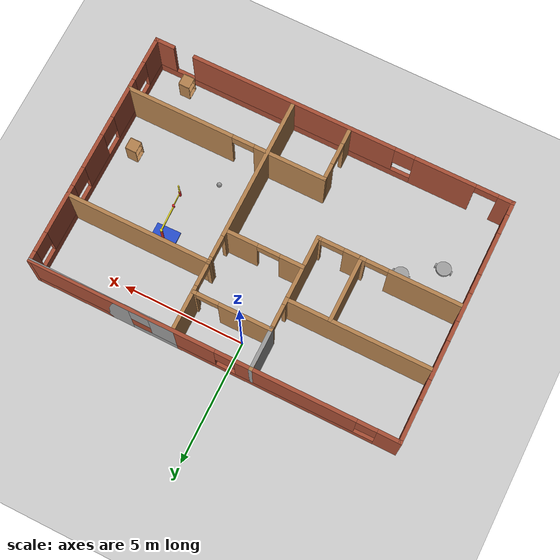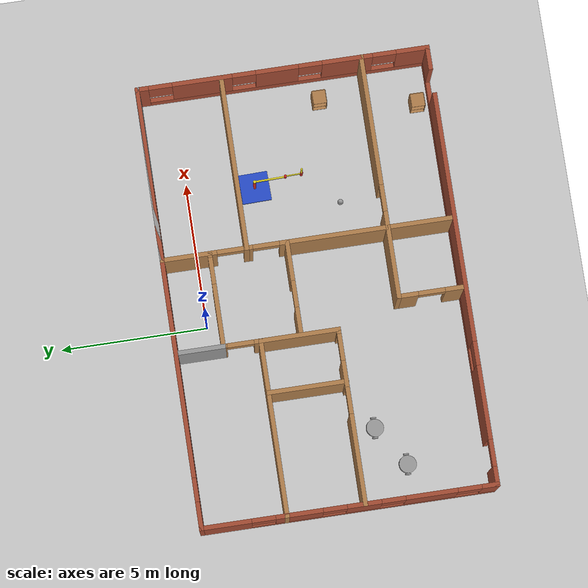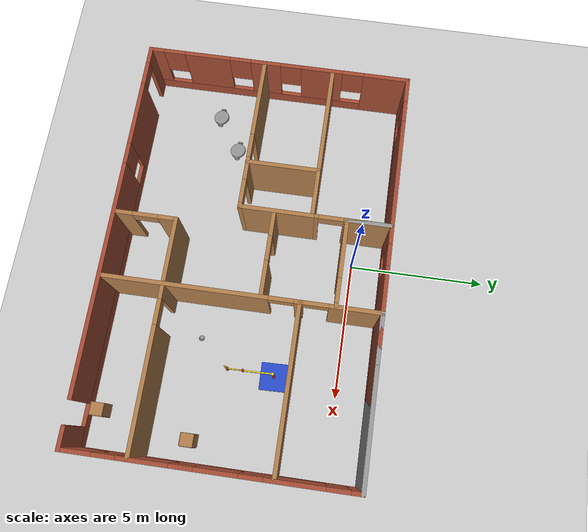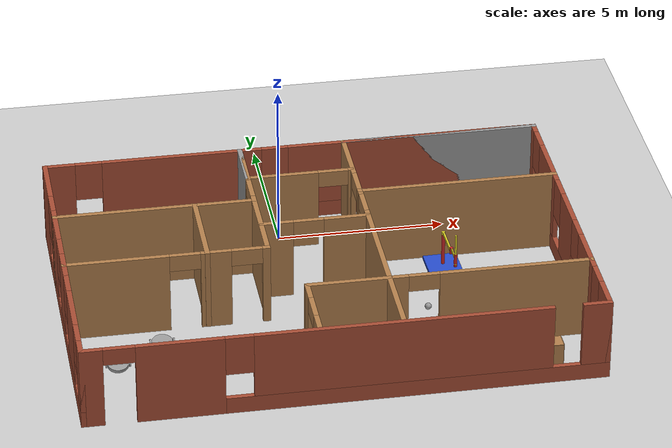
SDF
<sdf version="1.7">
 <world name="default">
  <light name="sun" type="directional">
   <pose>0 0 10 0 -0 0</pose>
   <diffuse>0.8 0.8 0.8 1</diffuse>
   <specular>0.2 0.2 0.2 1</specular>
   <attenuation>
    <range>1000</range>
    <constant>0.9</constant>
    <linear>0.01</linear>
    <quadratic>0.001</quadratic>
   </attenuation>
   <direction>-0.5 0.1 -0.9</direction>
   <spot><inner_angle>0</inner_angle><outer_angle>0</outer_angle><falloff>0</falloff></spot>
  </light>
  <model name="ground_plane">
   <static>1</static>
   <link name="link">
    <collision name="collision">
     <geometry><plane><normal>0 0 1</normal><size>100 100</size></plane></geometry>
     <surface>
      <contact><collide_bitmask>65535</collide_bitmask></contact>
      <friction><ode><mu>100</mu><mu2>50</mu2></ode></friction>
     </surface>
    </collision>
    <visual name="visual">
     <cast_shadows>0</cast_shadows>
     <geometry><plane><normal>0 0 1</normal><size>100 100</size></plane></geometry>
     <material>
      <script><uri>file://media/materials/scripts/gazebo.material</uri><name>Gazebo/Grey</name></script>
     </material>
    </visual>
   </link>
  </model>
  <gravity>0 0 -9.8</gravity>
  <magnetic_field>6e-06 2.3e-05 -4.2e-05</magnetic_field>
  <atmosphere type="adiabatic"/>
  <physics type="ode">
   <max_step_size>0.001</max_step_size>
   <real_time_factor>1</real_time_factor>
   <real_time_update_rate>1000</real_time_update_rate>
  </physics>
  <scene><ambient>0.4 0.4 0.4 1</ambient><background>0.7 0.7 0.7 1</background><shadows>1</shadows></scene>
  <spherical_coordinates>
   <surface_model>EARTH_WGS84</surface_model>
   <latitude_deg>0</latitude_deg>
   <longitude_deg>0</longitude_deg>
   <elevation>0</elevation>
   <heading_deg>0</heading_deg>
  </spherical_coordinates>
  <model name="building">
   <pose>0.591 -3.76 0 0 -0 0</pose>
   <link name="Wall_0">
    <pose>-7.425 -0 0 0 -0 -1.5708</pose>
    <visual name="Wall_0_Visual_0">
     <pose>-4.12676 0 1.25 0 -0 0</pose>
     <geometry><box><size>1.74647 0.15 2.5</size></box></geometry>
     <material>
      <script><uri>file://media/materials/scripts/gazebo.material</uri><name>Gazebo/Bricks</name></script>
      <ambient>0.913725 0.72549 0.431373 1</ambient>
     </material>
     <meta><layer>0</layer></meta>
    </visual>
    <collision name="Wall_0_Collision_0">
     <geometry><box><size>1.74647 0.15 2.5</size></box></geometry>
     <pose>-4.12676 0 1.25 0 -0 0</pose>
    </collision>
    <visual name="Wall_0_Visual_1">
     <pose>0.873237 0 0.25 0 -0 0</pose>
     <geometry><box><size>8.25353 0.15 0.5</size></box></geometry>
     <material>
      <script><uri>file://media/materials/scripts/gazebo.material</uri><name>Gazebo/Bricks</name></script>
      <ambient>0.913725 0.72549 0.431373 1</ambient>
     </material>
     <meta><layer>0</layer></meta>
    </visual>
    <collision name="Wall_0_Collision_1">
     <geometry><box><size>8.25353 0.15 0.5</size></box></geometry>
     <pose>0.873237 0 0.25 0 -0 0</pose>
    </collision>
    <visual name="Wall_0_Visual_2">
     <pose>-1.66683 0 1.5 0 -0 0</pose>
     <geometry><box><size>1.5734 0.15 2</size></box></geometry>
     <material>
      <script><uri>file://media/materials/scripts/gazebo.material</uri><name>Gazebo/Bricks</name></script>
      <ambient>0.913725 0.72549 0.431373 1</ambient>
     </material>
     <meta><layer>0</layer></meta>
    </visual>
    <collision name="Wall_0_Collision_2">
     <geometry><box><size>1.5734 0.15 2</size></box></geometry>
     <pose>-1.66683 0 1.5 0 -0 0</pose>
    </collision>
    <visual name="Wall_0_Visual_3">
     <pose>0.495383 0 1.5 0 -0 0</pose>
     <geometry><box><size>1.15102 0.15 2</size></box></geometry>
     <material>
      <script><uri>file://media/materials/scripts/gazebo.material</uri><name>Gazebo/Bricks</name></script>
      <ambient>0.913725 0.72549 0.431373 1</ambient>
     </material>
     <meta><layer>0</layer></meta>
    </visual>
    <collision name="Wall_0_Collision_3">
     <geometry><box><size>1.15102 0.15 2</size></box></geometry>
     <pose>0.495383 0 1.5 0 -0 0</pose>
    </collision>
    <visual name="Wall_0_Visual_4">
     <pose>2.73805 0 1.5 0 -0 0</pose>
     <geometry><box><size>1.73431 0.15 2</size></box></geometry>
     <material>
      <script><uri>file://media/materials/scripts/gazebo.material</uri><name>Gazebo/Bricks</name></script>
      <ambient>0.913725 0.72549 0.431373 1</ambient>
     </material>
     <meta><layer>0</layer></meta>
    </visual>
    <collision name="Wall_0_Collision_4">
     <geometry><box><size>1.73431 0.15 2</size></box></geometry>
     <pose>2.73805 0 1.5 0 -0 0</pose>
    </collision>
    <visual name="Wall_0_Visual_5">
     <pose>4.7026 0 1.5 0 -0 0</pose>
     <geometry><box><size>0.594798 0.15 2</size></box></geometry>
     <material>
      <script><uri>file://media/materials/scripts/gazebo.material</uri><name>Gazebo/Bricks</name></script>
      <ambient>0.913725 0.72549 0.431373 1</ambient>
     </material>
     <meta><layer>0</layer></meta>
    </visual>
    <collision name="Wall_0_Collision_5">
     <geometry><box><size>0.594798 0.15 2</size></box></geometry>
     <pose>4.7026 0 1.5 0 -0 0</pose>
    </collision>
    <visual name="Wall_0_Visual_6">
     <pose>-2.85353 0 1.9 0 -0 0</pose>
     <geometry><box><size>0.8 0.15 1.2</size></box></geometry>
     <material>
      <script><uri>file://media/materials/scripts/gazebo.material</uri><name>Gazebo/Bricks</name></script>
      <ambient>0.913725 0.72549 0.431373 1</ambient>
     </material>
     <meta><layer>0</layer></meta>
    </visual>
    <collision name="Wall_0_Collision_6">
     <geometry><box><size>0.8 0.15 1.2</size></box></geometry>
     <pose>-2.85353 0 1.9 0 -0 0</pose>
    </collision>
    <visual name="Wall_0_Visual_7">
     <pose>-0.480125 0 1.9 0 -0 0</pose>
     <geometry><box><size>0.8 0.15 1.2</size></box></geometry>
     <material>
      <script><uri>file://media/materials/scripts/gazebo.material</uri><name>Gazebo/Bricks</name></script>
      <ambient>0.913725 0.72549 0.431373 1</ambient>
     </material>
     <meta><layer>0</layer></meta>
    </visual>
    <collision name="Wall_0_Collision_7">
     <geometry><box><size>0.8 0.15 1.2</size></box></geometry>
     <pose>-0.480125 0 1.9 0 -0 0</pose>
    </collision>
    <visual name="Wall_0_Visual_8">
     <pose>1.47089 0 1.9 0 -0 0</pose>
     <geometry><box><size>0.8 0.15 1.2</size></box></geometry>
     <material>
      <script><uri>file://media/materials/scripts/gazebo.material</uri><name>Gazebo/Bricks</name></script>
      <ambient>0.913725 0.72549 0.431373 1</ambient>
     </material>
     <meta><layer>0</layer></meta>
    </visual>
    <collision name="Wall_0_Collision_8">
     <geometry><box><size>0.8 0.15 1.2</size></box></geometry>
     <pose>1.47089 0 1.9 0 -0 0</pose>
    </collision>
    <visual name="Wall_0_Visual_9">
     <pose>4.0052 0 1.9 0 -0 0</pose>
     <geometry><box><size>0.8 0.15 1.2</size></box></geometry>
     <material>
      <script><uri>file://media/materials/scripts/gazebo.material</uri><name>Gazebo/Bricks</name></script>
      <ambient>0.913725 0.72549 0.431373 1</ambient>
     </material>
     <meta><layer>0</layer></meta>
    </visual>
    <collision name="Wall_0_Collision_9">
     <geometry><box><size>0.8 0.15 1.2</size></box></geometry>
     <pose>4.0052 0 1.9 0 -0 0</pose>
    </collision>
   </link>
   <link name="Wall_10">
    <collision name="Wall_10_Collision">
     <geometry><box><size>6 0.15 2.5</size></box></geometry>
     <pose>0 0 1.25 0 -0 0</pose>
    </collision>
    <visual name="Wall_10_Visual">
     <pose>0 0 1.25 0 -0 0</pose>
     <geometry><box><size>6 0.15 2.5</size></box></geometry>
     <material>
      <script><uri>file://media/materials/scripts/gazebo.material</uri><name>Gazebo/Wood</name></script>
      <ambient>0 0 0 1</ambient>
     </material>
     <meta><layer>0</layer></meta>
    </visual>
    <pose>-4.5 2.075 0 0 -0 3.14159</pose>
   </link>
   <link name="Wall_12">
    <pose>4.5 4.925 0 0 -0 3.14159</pose>
    <visual name="Wall_12_Visual_0">
     <pose>-0.916939 0 1.25 0 -0 0</pose>
     <geometry><box><size>4.16612 0.15 2.5</size></box></geometry>
     <material>
      <script><uri>file://media/materials/scripts/gazebo.material</uri><name>Gazebo/Grey</name></script>
      <ambient>1 1 1 1</ambient>
     </material>
     <meta><layer>0</layer></meta>
    </visual>
    <collision name="Wall_12_Collision_0">
     <geometry><box><size>4.16612 0.15 2.5</size></box></geometry>
     <pose>-0.916939 0 1.25 0 -0 0</pose>
    </collision>
    <visual name="Wall_12_Visual_1">
     <pose>2.08306 0 0.25 0 -0 0</pose>
     <geometry><box><size>1.83388 0.15 0.5</size></box></geometry>
     <material>
      <script><uri>file://media/materials/scripts/gazebo.material</uri><name>Gazebo/Grey</name></script>
      <ambient>1 1 1 1</ambient>
     </material>
     <meta><layer>0</layer></meta>
    </visual>
    <collision name="Wall_12_Collision_1">
     <geometry><box><size>1.83388 0.15 0.5</size></box></geometry>
     <pose>2.08306 0 0.25 0 -0 0</pose>
    </collision>
    <visual name="Wall_12_Visual_2">
     <pose>2.48306 0 1.5 0 -0 0</pose>
     <geometry><box><size>1.03388 0.15 2</size></box></geometry>
     <material>
      <script><uri>file://media/materials/scripts/gazebo.material</uri><name>Gazebo/Grey</name></script>
      <ambient>1 1 1 1</ambient>
     </material>
     <meta><layer>0</layer></meta>
    </visual>
    <collision name="Wall_12_Collision_2">
     <geometry><box><size>1.03388 0.15 2</size></box></geometry>
     <pose>2.48306 0 1.5 0 -0 0</pose>
    </collision>
    <visual name="Wall_12_Visual_3">
     <pose>1.56612 0 1.9 0 -0 0</pose>
     <geometry><box><size>0.8 0.15 1.2</size></box></geometry>
     <material>
      <script><uri>file://media/materials/scripts/gazebo.material</uri><name>Gazebo/Grey</name></script>
      <ambient>1 1 1 1</ambient>
     </material>
     <meta><layer>0</layer></meta>
    </visual>
    <collision name="Wall_12_Collision_3">
     <geometry><box><size>0.8 0.15 1.2</size></box></geometry>
     <pose>1.56612 0 1.9 0 -0 0</pose>
    </collision>
   </link>
   <link name="Wall_13">
    <pose>1.575 3.5 0 0 -0 -1.5708</pose>
    <visual name="Wall_13_Visual_0">
     <pose>-0.541139 0 1.25 0 -0 0</pose>
     <geometry><box><size>1.91772 0.15 2.5</size></box></geometry>
     <material>
      <script><uri>file://media/materials/scripts/gazebo.material</uri><name>Gazebo/Wood</name></script>
      <ambient>0 0 0 1</ambient>
     </material>
     <meta><layer>0</layer></meta>
    </visual>
    <collision name="Wall_13_Collision_0">
     <geometry><box><size>1.91772 0.15 2.5</size></box></geometry>
     <pose>-0.541139 0 1.25 0 -0 0</pose>
    </collision>
    <visual name="Wall_13_Visual_1">
     <pose>1.40886 0 1.25 0 -0 0</pose>
     <geometry><box><size>0.182277 0.15 2.5</size></box></geometry>
     <material>
      <script><uri>file://media/materials/scripts/gazebo.material</uri><name>Gazebo/Wood</name></script>
      <ambient>0 0 0 1</ambient>
     </material>
     <meta><layer>0</layer></meta>
    </visual>
    <collision name="Wall_13_Collision_1">
     <geometry><box><size>0.182277 0.15 2.5</size></box></geometry>
     <pose>1.40886 0 1.25 0 -0 0</pose>
    </collision>
    <visual name="Wall_13_Visual_2">
     <pose>0.867723 0 2.25 0 -0 0</pose>
     <geometry><box><size>0.9 0.15 0.5</size></box></geometry>
     <material>
      <script><uri>file://media/materials/scripts/gazebo.material</uri><name>Gazebo/Wood</name></script>
      <ambient>0 0 0 1</ambient>
     </material>
     <meta><layer>0</layer></meta>
    </visual>
    <collision name="Wall_13_Collision_2">
     <geometry><box><size>0.9 0.15 0.5</size></box></geometry>
     <pose>0.867723 0 2.25 0 -0 0</pose>
    </collision>
   </link>
   <link name="Wall_16">
    <collision name="Wall_16_Collision">
     <geometry><box><size>6 0.15 2.5</size></box></geometry>
     <pose>0 0 1.25 0 -0 0</pose>
    </collision>
    <visual name="Wall_16_Visual">
     <pose>0 0 1.25 0 -0 0</pose>
     <geometry><box><size>6 0.15 2.5</size></box></geometry>
     <material>
      <script><uri>file://media/materials/scripts/gazebo.material</uri><name>Gazebo/Wood</name></script>
      <ambient>0 0 0 1</ambient>
     </material>
     <meta><layer>0</layer></meta>
    </visual>
    <pose>4.5 2.075 0 0 -0 0</pose>
   </link>
   <link name="Wall_18">
    <collision name="Wall_18_Collision">
     <geometry><box><size>1.75 0.15 2.5</size></box></geometry>
     <pose>0 0 1.25 0 -0 0</pose>
    </collision>
    <visual name="Wall_18_Visual">
     <pose>0 0 1.25 0 -0 0</pose>
     <geometry><box><size>1.75 0.15 2.5</size></box></geometry>
     <material>
      <script><uri>file://media/materials/scripts/gazebo.material</uri><name>Gazebo/Grey</name></script>
      <ambient>1 1 1 1</ambient>
     </material>
     <meta><layer>0</layer></meta>
    </visual>
    <pose>-1.575 4.125 0 0 -0 -1.5708</pose>
   </link>
   <link name="Wall_19">
    <pose>-0.025 3.325 0 0 -0 0</pose>
    <visual name="Wall_19_Visual_0">
     <pose>-0.533569 0 1.25 0 -0 0</pose>
     <geometry><box><size>2.18286 0.15 2.5</size></box></geometry>
     <material>
      <script><uri>file://media/materials/scripts/gazebo.material</uri><name>Gazebo/Wood</name></script>
      <ambient>0 0 0 1</ambient>
     </material>
     <meta><layer>0</layer></meta>
    </visual>
    <collision name="Wall_19_Collision_0">
     <geometry><box><size>2.18286 0.15 2.5</size></box></geometry>
     <pose>-0.533569 0 1.25 0 -0 0</pose>
    </collision>
    <visual name="Wall_19_Visual_1">
     <pose>1.54143 0 1.25 0 -0 0</pose>
     <geometry><box><size>0.167139 0.15 2.5</size></box></geometry>
     <material>
      <script><uri>file://media/materials/scripts/gazebo.material</uri><name>Gazebo/Wood</name></script>
      <ambient>0 0 0 1</ambient>
     </material>
     <meta><layer>0</layer></meta>
    </visual>
    <collision name="Wall_19_Collision_1">
     <geometry><box><size>0.167139 0.15 2.5</size></box></geometry>
     <pose>1.54143 0 1.25 0 -0 0</pose>
    </collision>
    <visual name="Wall_19_Visual_2">
     <pose>1.00786 0 2.25 0 -0 0</pose>
     <geometry><box><size>0.9 0.15 0.5</size></box></geometry>
     <material>
      <script><uri>file://media/materials/scripts/gazebo.material</uri><name>Gazebo/Wood</name></script>
      <ambient>0 0 0 1</ambient>
     </material>
     <meta><layer>0</layer></meta>
    </visual>
    <collision name="Wall_19_Collision_2">
     <geometry><box><size>0.9 0.15 0.5</size></box></geometry>
     <pose>1.00786 0 2.25 0 -0 0</pose>
    </collision>
   </link>
   <link name="Wall_2">
    <pose>0 4.925 0 0 -0 0</pose>
    <visual name="Wall_2_Visual_0">
     <pose>-7.01867 0 1.25 0 -0 0</pose>
     <geometry><box><size>0.962657 0.15 2.5</size></box></geometry>
     <material>
      <script><uri>file://media/materials/scripts/gazebo.material</uri><name>Gazebo/Bricks</name></script>
      <ambient>0.435294 0.796078 0.67451 1</ambient>
     </material>
     <meta><layer>0</layer></meta>
    </visual>
    <collision name="Wall_2_Collision_0">
     <geometry><box><size>0.962657 0.15 2.5</size></box></geometry>
     <pose>-7.01867 0 1.25 0 -0 0</pose>
    </collision>
    <visual name="Wall_2_Visual_1">
     <pose>0.481329 0 0.25 0 -0 0</pose>
     <geometry><box><size>14.0373 0.15 0.5</size></box></geometry>
     <material>
      <script><uri>file://media/materials/scripts/gazebo.material</uri><name>Gazebo/Bricks</name></script>
      <ambient>0.435294 0.796078 0.67451 1</ambient>
     </material>
     <meta><layer>0</layer></meta>
    </visual>
    <collision name="Wall_2_Collision_1">
     <geometry><box><size>14.0373 0.15 0.5</size></box></geometry>
     <pose>0.481329 0 0.25 0 -0 0</pose>
    </collision>
    <visual name="Wall_2_Visual_2">
     <pose>-3.3315 0 1.5 0 -0 0</pose>
     <geometry><box><size>4.81169 0.15 2</size></box></geometry>
     <material>
      <script><uri>file://media/materials/scripts/gazebo.material</uri><name>Gazebo/Bricks</name></script>
      <ambient>0.435294 0.796078 0.67451 1</ambient>
     </material>
     <meta><layer>0</layer></meta>
    </visual>
    <collision name="Wall_2_Collision_2">
     <geometry><box><size>4.81169 0.15 2</size></box></geometry>
     <pose>-3.3315 0 1.5 0 -0 0</pose>
    </collision>
    <visual name="Wall_2_Visual_3">
     <pose>3.68717 0 1.5 0 -0 0</pose>
     <geometry><box><size>7.62566 0.15 2</size></box></geometry>
     <material>
      <script><uri>file://media/materials/scripts/gazebo.material</uri><name>Gazebo/Bricks</name></script>
      <ambient>0.435294 0.796078 0.67451 1</ambient>
     </material>
     <meta><layer>0</layer></meta>
    </visual>
    <collision name="Wall_2_Collision_3">
     <geometry><box><size>7.62566 0.15 2</size></box></geometry>
     <pose>3.68717 0 1.5 0 -0 0</pose>
    </collision>
    <visual name="Wall_2_Visual_4">
     <pose>-6.13734 0 1.9 0 -0 0</pose>
     <geometry><box><size>0.8 0.15 1.2</size></box></geometry>
     <material>
      <script><uri>file://media/materials/scripts/gazebo.material</uri><name>Gazebo/Bricks</name></script>
      <ambient>0.435294 0.796078 0.67451 1</ambient>
     </material>
     <meta><layer>0</layer></meta>
    </visual>
    <collision name="Wall_2_Collision_4">
     <geometry><box><size>0.8 0.15 1.2</size></box></geometry>
     <pose>-6.13734 0 1.9 0 -0 0</pose>
    </collision>
    <visual name="Wall_2_Visual_5">
     <pose>-0.525656 0 1.9 0 -0 0</pose>
     <geometry><box><size>0.8 0.15 1.2</size></box></geometry>
     <material>
      <script><uri>file://media/materials/scripts/gazebo.material</uri><name>Gazebo/Bricks</name></script>
      <ambient>0.435294 0.796078 0.67451 1</ambient>
     </material>
     <meta><layer>0</layer></meta>
    </visual>
    <collision name="Wall_2_Collision_5">
     <geometry><box><size>0.8 0.15 1.2</size></box></geometry>
     <pose>-0.525656 0 1.9 0 -0 0</pose>
    </collision>
   </link>
   <link name="Wall_21">
    <collision name="Wall_21_Collision">
     <geometry><box><size>2.75 0.15 2.5</size></box></geometry>
     <pose>0 0 1.25 0 -0 0</pose>
    </collision>
    <visual name="Wall_21_Visual">
     <pose>0 0 1.25 0 -0 0</pose>
     <geometry><box><size>2.75 0.15 2.5</size></box></geometry>
     <material>
      <script><uri>file://media/materials/scripts/gazebo.material</uri><name>Gazebo/Wood</name></script>
      <ambient>0 0 0 1</ambient>
     </material>
     <meta><layer>0</layer></meta>
    </visual>
    <pose>-1.575 0.775 0 0 -0 -1.5708</pose>
   </link>
   <link name="Wall_22">
    <pose>-4.5 -0.525 0 0 -0 3.14159</pose>
    <visual name="Wall_22_Visual_0">
     <pose>-2.88752 0 1.25 0 -0 0</pose>
     <geometry><box><size>0.224969 0.15 2.5</size></box></geometry>
     <material>
      <script><uri>file://media/materials/scripts/gazebo.material</uri><name>Gazebo/Wood</name></script>
      <ambient>0 0 0 1</ambient>
     </material>
     <meta><layer>0</layer></meta>
    </visual>
    <collision name="Wall_22_Collision_0">
     <geometry><box><size>0.224969 0.15 2.5</size></box></geometry>
     <pose>-2.88752 0 1.25 0 -0 0</pose>
    </collision>
    <visual name="Wall_22_Visual_1">
     <pose>-1.42998 0 1.25 0 -0 0</pose>
     <geometry><box><size>0.890108 0.15 2.5</size></box></geometry>
     <material>
      <script><uri>file://media/materials/scripts/gazebo.material</uri><name>Gazebo/Wood</name></script>
      <ambient>0 0 0 1</ambient>
     </material>
     <meta><layer>0</layer></meta>
    </visual>
    <collision name="Wall_22_Collision_1">
     <geometry><box><size>0.890108 0.15 2.5</size></box></geometry>
     <pose>-1.42998 0 1.25 0 -0 0</pose>
    </collision>
    <visual name="Wall_22_Visual_2">
     <pose>1.45754 0 1.25 0 -0 0</pose>
     <geometry><box><size>3.08492 0.15 2.5</size></box></geometry>
     <material>
      <script><uri>file://media/materials/scripts/gazebo.material</uri><name>Gazebo/Wood</name></script>
      <ambient>0 0 0 1</ambient>
     </material>
     <meta><layer>0</layer></meta>
    </visual>
    <collision name="Wall_22_Collision_2">
     <geometry><box><size>3.08492 0.15 2.5</size></box></geometry>
     <pose>1.45754 0 1.25 0 -0 0</pose>
    </collision>
    <visual name="Wall_22_Visual_3">
     <pose>-2.32503 0 2.25 0 -0 0</pose>
     <geometry><box><size>0.9 0.15 0.5</size></box></geometry>
     <material>
      <script><uri>file://media/materials/scripts/gazebo.material</uri><name>Gazebo/Wood</name></script>
      <ambient>0 0 0 1</ambient>
     </material>
     <meta><layer>0</layer></meta>
    </visual>
    <collision name="Wall_22_Collision_3">
     <geometry><box><size>0.9 0.15 0.5</size></box></geometry>
     <pose>-2.32503 0 2.25 0 -0 0</pose>
    </collision>
    <visual name="Wall_22_Visual_4">
     <pose>-0.534923 0 2.25 0 -0 0</pose>
     <geometry><box><size>0.9 0.15 0.5</size></box></geometry>
     <material>
      <script><uri>file://media/materials/scripts/gazebo.material</uri><name>Gazebo/Wood</name></script>
      <ambient>0 0 0 1</ambient>
     </material>
     <meta><layer>0</layer></meta>
    </visual>
    <collision name="Wall_22_Collision_4">
     <geometry><box><size>0.9 0.15 0.5</size></box></geometry>
     <pose>-0.534923 0 2.25 0 -0 0</pose>
    </collision>
   </link>
   <link name="Wall_26">
    <collision name="Wall_26_Collision">
     <geometry><box><size>2.75 0.15 2.5</size></box></geometry>
     <pose>0 0 1.25 0 -0 0</pose>
    </collision>
    <visual name="Wall_26_Visual">
     <pose>0 0 1.25 0 -0 0</pose>
     <geometry><box><size>2.75 0.15 2.5</size></box></geometry>
     <material>
      <script><uri>file://media/materials/scripts/gazebo.material</uri><name>Gazebo/Wood</name></script>
      <ambient>0 0 0 1</ambient>
     </material>
     <meta><layer>0</layer></meta>
    </visual>
    <pose>-3.32144 0.769097 0 0 -0 -1.5708</pose>
   </link>
   <link name="Wall_28">
    <pose>1.575 -1.35 0 0 -0 -1.5708</pose>
    <visual name="Wall_28_Visual_0">
     <pose>-3.36273 0 1.25 0 -0 0</pose>
     <geometry><box><size>0.274537 0.15 2.5</size></box></geometry>
     <material>
      <script><uri>file://media/materials/scripts/gazebo.material</uri><name>Gazebo/Wood</name></script>
      <ambient>0 0 0 1</ambient>
     </material>
     <meta><layer>0</layer></meta>
    </visual>
    <collision name="Wall_28_Collision_0">
     <geometry><box><size>0.274537 0.15 2.5</size></box></geometry>
     <pose>-3.36273 0 1.25 0 -0 0</pose>
    </collision>
    <visual name="Wall_28_Visual_1">
     <pose>0.587269 0 1.25 0 -0 0</pose>
     <geometry><box><size>5.82546 0.15 2.5</size></box></geometry>
     <material>
      <script><uri>file://media/materials/scripts/gazebo.material</uri><name>Gazebo/Wood</name></script>
      <ambient>0 0 0 1</ambient>
     </material>
     <meta><layer>0</layer></meta>
    </visual>
    <collision name="Wall_28_Collision_1">
     <geometry><box><size>5.82546 0.15 2.5</size></box></geometry>
     <pose>0.587269 0 1.25 0 -0 0</pose>
    </collision>
    <visual name="Wall_28_Visual_2">
     <pose>-2.77546 0 2.25 0 -0 0</pose>
     <geometry><box><size>0.9 0.15 0.5</size></box></geometry>
     <material>
      <script><uri>file://media/materials/scripts/gazebo.material</uri><name>Gazebo/Wood</name></script>
      <ambient>0 0 0 1</ambient>
     </material>
     <meta><layer>0</layer></meta>
    </visual>
    <collision name="Wall_28_Collision_2">
     <geometry><box><size>0.9 0.15 0.5</size></box></geometry>
     <pose>-2.77546 0 2.25 0 -0 0</pose>
    </collision>
   </link>
   <link name="Wall_31">
    <pose>-0.001448 0.721488 0 0 -0 0</pose>
    <visual name="Wall_31_Visual_0">
     <pose>-1.12864 0 1.25 0 -0 0</pose>
     <geometry><box><size>0.992723 0.15 2.5</size></box></geometry>
     <material>
      <script><uri>file://media/materials/scripts/gazebo.material</uri><name>Gazebo/Wood</name></script>
      <ambient>0 0 0 1</ambient>
     </material>
     <meta><layer>0</layer></meta>
    </visual>
    <collision name="Wall_31_Collision_0">
     <geometry><box><size>0.992723 0.15 2.5</size></box></geometry>
     <pose>-1.12864 0 1.25 0 -0 0</pose>
    </collision>
    <visual name="Wall_31_Visual_1">
     <pose>0.946361 0 1.25 0 -0 0</pose>
     <geometry><box><size>1.35728 0.15 2.5</size></box></geometry>
     <material>
      <script><uri>file://media/materials/scripts/gazebo.material</uri><name>Gazebo/Wood</name></script>
      <ambient>0 0 0 1</ambient>
     </material>
     <meta><layer>0</layer></meta>
    </visual>
    <collision name="Wall_31_Collision_1">
     <geometry><box><size>1.35728 0.15 2.5</size></box></geometry>
     <pose>0.946361 0 1.25 0 -0 0</pose>
    </collision>
    <visual name="Wall_31_Visual_2">
     <pose>-0.182277 0 2.25 0 -0 0</pose>
     <geometry><box><size>0.9 0.15 0.5</size></box></geometry>
     <material>
      <script><uri>file://media/materials/scripts/gazebo.material</uri><name>Gazebo/Wood</name></script>
      <ambient>0 0 0 1</ambient>
     </material>
     <meta><layer>0</layer></meta>
    </visual>
    <collision name="Wall_31_Collision_2">
     <geometry><box><size>0.9 0.15 0.5</size></box></geometry>
     <pose>-0.182277 0 2.25 0 -0 0</pose>
    </collision>
   </link>
   <link name="Wall_33">
    <pose>4.49116 -2.67771 0 0 -0 0</pose>
    <visual name="Wall_33_Visual_0">
     <pose>-2.68466 0 1.25 0 -0 0</pose>
     <geometry><box><size>0.630678 0.15 2.5</size></box></geometry>
     <material>
      <script><uri>file://media/materials/scripts/gazebo.material</uri><name>Gazebo/Wood</name></script>
      <ambient>0 0 0 1</ambient>
     </material>
     <meta><layer>0</layer></meta>
    </visual>
    <collision name="Wall_33_Collision_0">
     <geometry><box><size>0.630678 0.15 2.5</size></box></geometry>
     <pose>-2.68466 0 1.25 0 -0 0</pose>
    </collision>
    <visual name="Wall_33_Visual_1">
     <pose>0.765339 0 1.25 0 -0 0</pose>
     <geometry><box><size>4.46932 0.15 2.5</size></box></geometry>
     <material>
      <script><uri>file://media/materials/scripts/gazebo.material</uri><name>Gazebo/Wood</name></script>
      <ambient>0 0 0 1</ambient>
     </material>
     <meta><layer>0</layer></meta>
    </visual>
    <collision name="Wall_33_Collision_1">
     <geometry><box><size>4.46932 0.15 2.5</size></box></geometry>
     <pose>0.765339 0 1.25 0 -0 0</pose>
    </collision>
    <visual name="Wall_33_Visual_2">
     <pose>-1.91932 0 2.25 0 -0 0</pose>
     <geometry><box><size>0.9 0.15 0.5</size></box></geometry>
     <material>
      <script><uri>file://media/materials/scripts/gazebo.material</uri><name>Gazebo/Wood</name></script>
      <ambient>0 0 0 1</ambient>
     </material>
     <meta><layer>0</layer></meta>
    </visual>
    <collision name="Wall_33_Collision_2">
     <geometry><box><size>0.9 0.15 0.5</size></box></geometry>
     <pose>-1.91932 0 2.25 0 -0 0</pose>
    </collision>
   </link>
   <link name="Wall_35">
    <collision name="Wall_35_Collision">
     <geometry><box><size>2.5 0.15 2.5</size></box></geometry>
     <pose>0 0 1.25 0 -0 0</pose>
    </collision>
    <visual name="Wall_35_Visual">
     <pose>0 0 1.25 0 -0 0</pose>
     <geometry><box><size>2.5 0.15 2.5</size></box></geometry>
     <material>
      <script><uri>file://media/materials/scripts/gazebo.material</uri><name>Gazebo/Wood</name></script>
      <ambient>0 0 0 1</ambient>
     </material>
     <meta><layer>0</layer></meta>
    </visual>
    <pose>0.391155 -2.67771 0 0 -0 3.14159</pose>
   </link>
   <link name="Wall_36">
    <pose>-0.783845 -3.72771 0 0 -0 -1.5708</pose>
    <visual name="Wall_36_Visual_0">
     <pose>-0.759377 0 1.25 0 -0 0</pose>
     <geometry><box><size>0.731247 0.15 2.5</size></box></geometry>
     <material>
      <script><uri>file://media/materials/scripts/gazebo.material</uri><name>Gazebo/Wood</name></script>
      <ambient>0 0 0 1</ambient>
     </material>
     <meta><layer>0</layer></meta>
    </visual>
    <collision name="Wall_36_Collision_0">
     <geometry><box><size>0.731247 0.15 2.5</size></box></geometry>
     <pose>-0.759377 0 1.25 0 -0 0</pose>
    </collision>
    <visual name="Wall_36_Visual_1">
     <pose>0.815623 0 1.25 0 -0 0</pose>
     <geometry><box><size>0.618753 0.15 2.5</size></box></geometry>
     <material>
      <script><uri>file://media/materials/scripts/gazebo.material</uri><name>Gazebo/Wood</name></script>
      <ambient>0 0 0 1</ambient>
     </material>
     <meta><layer>0</layer></meta>
    </visual>
    <collision name="Wall_36_Collision_1">
     <geometry><box><size>0.618753 0.15 2.5</size></box></geometry>
     <pose>0.815623 0 1.25 0 -0 0</pose>
    </collision>
    <visual name="Wall_36_Visual_2">
     <pose>0.056247 0 2.25 0 -0 0</pose>
     <geometry><box><size>0.9 0.15 0.5</size></box></geometry>
     <material>
      <script><uri>file://media/materials/scripts/gazebo.material</uri><name>Gazebo/Wood</name></script>
      <ambient>0 0 0 1</ambient>
     </material>
     <meta><layer>0</layer></meta>
    </visual>
    <collision name="Wall_36_Collision_2">
     <geometry><box><size>0.9 0.15 0.5</size></box></geometry>
     <pose>0.056247 0 2.25 0 -0 0</pose>
    </collision>
   </link>
   <link name="Wall_4">
    <pose>7.425 -0 0 0 -0 -1.5708</pose>
    <visual name="Wall_4_Visual_0">
     <pose>-4.7704 0 1.25 0 -0 0</pose>
     <geometry><box><size>0.459205 0.15 2.5</size></box></geometry>
     <material>
      <script><uri>file://media/materials/scripts/gazebo.material</uri><name>Gazebo/Bricks</name></script>
      <ambient>0.913725 0.72549 0.431373 1</ambient>
     </material>
     <meta><layer>0</layer></meta>
    </visual>
    <collision name="Wall_4_Collision_0">
     <geometry><box><size>0.459205 0.15 2.5</size></box></geometry>
     <pose>-4.7704 0 1.25 0 -0 0</pose>
    </collision>
    <visual name="Wall_4_Visual_1">
     <pose>0.229603 0 0.25 0 -0 0</pose>
     <geometry><box><size>9.54079 0.15 0.5</size></box></geometry>
     <material>
      <script><uri>file://media/materials/scripts/gazebo.material</uri><name>Gazebo/Bricks</name></script>
      <ambient>0.913725 0.72549 0.431373 1</ambient>
     </material>
     <meta><layer>0</layer></meta>
    </visual>
    <collision name="Wall_4_Collision_1">
     <geometry><box><size>9.54079 0.15 0.5</size></box></geometry>
     <pose>0.229603 0 0.25 0 -0 0</pose>
    </collision>
    <visual name="Wall_4_Visual_2">
     <pose>-2.72279 0 1.5 0 -0 0</pose>
     <geometry><box><size>2.03601 0.15 2</size></box></geometry>
     <material>
      <script><uri>file://media/materials/scripts/gazebo.material</uri><name>Gazebo/Bricks</name></script>
      <ambient>0.913725 0.72549 0.431373 1</ambient>
     </material>
     <meta><layer>0</layer></meta>
    </visual>
    <collision name="Wall_4_Collision_2">
     <geometry><box><size>2.03601 0.15 2</size></box></geometry>
     <pose>-2.72279 0 1.5 0 -0 0</pose>
    </collision>
    <visual name="Wall_4_Visual_3">
     <pose>-0.178421 0 1.5 0 -0 0</pose>
     <geometry><box><size>1.45272 0.15 2</size></box></geometry>
     <material>
      <script><uri>file://media/materials/scripts/gazebo.material</uri><name>Gazebo/Bricks</name></script>
      <ambient>0.913725 0.72549 0.431373 1</ambient>
     </material>
     <meta><layer>0</layer></meta>
    </visual>
    <collision name="Wall_4_Collision_3">
     <geometry><box><size>1.45272 0.15 2</size></box></geometry>
     <pose>-0.178421 0 1.5 0 -0 0</pose>
    </collision>
    <visual name="Wall_4_Visual_4">
     <pose>2.20504 0 1.5 0 -0 0</pose>
     <geometry><box><size>1.7142 0.15 2</size></box></geometry>
     <material>
      <script><uri>file://media/materials/scripts/gazebo.material</uri><name>Gazebo/Bricks</name></script>
      <ambient>0.913725 0.72549 0.431373 1</ambient>
     </material>
     <meta><layer>0</layer></meta>
    </visual>
    <collision name="Wall_4_Collision_4">
     <geometry><box><size>1.7142 0.15 2</size></box></geometry>
     <pose>2.20504 0 1.5 0 -0 0</pose>
    </collision>
    <visual name="Wall_4_Visual_5">
     <pose>4.43107 0 1.5 0 -0 0</pose>
     <geometry><box><size>1.13786 0.15 2</size></box></geometry>
     <material>
      <script><uri>file://media/materials/scripts/gazebo.material</uri><name>Gazebo/Bricks</name></script>
      <ambient>0.913725 0.72549 0.431373 1</ambient>
     </material>
     <meta><layer>0</layer></meta>
    </visual>
    <collision name="Wall_4_Collision_5">
     <geometry><box><size>1.13786 0.15 2</size></box></geometry>
     <pose>4.43107 0 1.5 0 -0 0</pose>
    </collision>
    <visual name="Wall_4_Visual_6">
     <pose>-4.14079 0 1.9 0 -0 0</pose>
     <geometry><box><size>0.8 0.15 1.2</size></box></geometry>
     <material>
      <script><uri>file://media/materials/scripts/gazebo.material</uri><name>Gazebo/Bricks</name></script>
      <ambient>0.913725 0.72549 0.431373 1</ambient>
     </material>
     <meta><layer>0</layer></meta>
    </visual>
    <collision name="Wall_4_Collision_6">
     <geometry><box><size>0.8 0.15 1.2</size></box></geometry>
     <pose>-4.14079 0 1.9 0 -0 0</pose>
    </collision>
    <visual name="Wall_4_Visual_7">
     <pose>-1.30478 0 1.9 0 -0 0</pose>
     <geometry><box><size>0.8 0.15 1.2</size></box></geometry>
     <material>
      <script><uri>file://media/materials/scripts/gazebo.material</uri><name>Gazebo/Bricks</name></script>
      <ambient>0.913725 0.72549 0.431373 1</ambient>
     </material>
     <meta><layer>0</layer></meta>
    </visual>
    <collision name="Wall_4_Collision_7">
     <geometry><box><size>0.8 0.15 1.2</size></box></geometry>
     <pose>-1.30478 0 1.9 0 -0 0</pose>
    </collision>
    <visual name="Wall_4_Visual_8">
     <pose>0.947939 0 1.9 0 -0 0</pose>
     <geometry><box><size>0.8 0.15 1.2</size></box></geometry>
     <material>
      <script><uri>file://media/materials/scripts/gazebo.material</uri><name>Gazebo/Bricks</name></script>
      <ambient>0.913725 0.72549 0.431373 1</ambient>
     </material>
     <meta><layer>0</layer></meta>
    </visual>
    <collision name="Wall_4_Collision_8">
     <geometry><box><size>0.8 0.15 1.2</size></box></geometry>
     <pose>0.947939 0 1.9 0 -0 0</pose>
    </collision>
    <visual name="Wall_4_Visual_9">
     <pose>3.46213 0 1.9 0 -0 0</pose>
     <geometry><box><size>0.8 0.15 1.2</size></box></geometry>
     <material>
      <script><uri>file://media/materials/scripts/gazebo.material</uri><name>Gazebo/Bricks</name></script>
      <ambient>0.913725 0.72549 0.431373 1</ambient>
     </material>
     <meta><layer>0</layer></meta>
    </visual>
    <collision name="Wall_4_Collision_9">
     <geometry><box><size>0.8 0.15 1.2</size></box></geometry>
     <pose>3.46213 0 1.9 0 -0 0</pose>
    </collision>
   </link>
   <link name="Wall_6">
    <pose>0 -4.925 0 0 -0 0</pose>
    <visual name="Wall_6_Visual_0">
     <pose>-7.16435 0 1.25 0 -0 0</pose>
     <geometry><box><size>0.671294 0.15 2.5</size></box></geometry>
     <material>
      <script><uri>file://media/materials/scripts/gazebo.material</uri><name>Gazebo/Bricks</name></script>
      <ambient>0.913725 0.72549 0.431373 1</ambient>
     </material>
     <meta><layer>0</layer></meta>
    </visual>
    <collision name="Wall_6_Collision_0">
     <geometry><box><size>0.671294 0.15 2.5</size></box></geometry>
     <pose>-7.16435 0 1.25 0 -0 0</pose>
    </collision>
    <visual name="Wall_6_Visual_1">
     <pose>-4.68428 0 1.25 0 -0 0</pose>
     <geometry><box><size>2.48885 0.15 2.5</size></box></geometry>
     <material>
      <script><uri>file://media/materials/scripts/gazebo.material</uri><name>Gazebo/Bricks</name></script>
      <ambient>0.913725 0.72549 0.431373 1</ambient>
     </material>
     <meta><layer>0</layer></meta>
    </visual>
    <collision name="Wall_6_Collision_1">
     <geometry><box><size>2.48885 0.15 2.5</size></box></geometry>
     <pose>-4.68428 0 1.25 0 -0 0</pose>
    </collision>
    <visual name="Wall_6_Visual_2">
     <pose>2.03007 0 0.25 0 -0 0</pose>
     <geometry><box><size>10.9399 0.15 0.5</size></box></geometry>
     <material>
      <script><uri>file://media/materials/scripts/gazebo.material</uri><name>Gazebo/Bricks</name></script>
      <ambient>0.913725 0.72549 0.431373 1</ambient>
     </material>
     <meta><layer>0</layer></meta>
    </visual>
    <collision name="Wall_6_Collision_2">
     <geometry><box><size>10.9399 0.15 0.5</size></box></geometry>
     <pose>2.03007 0 0.25 0 -0 0</pose>
    </collision>
    <visual name="Wall_6_Visual_3">
     <pose>1.60638 0 1.5 0 -0 0</pose>
     <geometry><box><size>8.49247 0.15 2</size></box></geometry>
     <material>
      <script><uri>file://media/materials/scripts/gazebo.material</uri><name>Gazebo/Bricks</name></script>
      <ambient>0.913725 0.72549 0.431373 1</ambient>
     </material>
     <meta><layer>0</layer></meta>
    </visual>
    <collision name="Wall_6_Collision_3">
     <geometry><box><size>8.49247 0.15 2</size></box></geometry>
     <pose>1.60638 0 1.5 0 -0 0</pose>
    </collision>
    <visual name="Wall_6_Visual_4">
     <pose>7.07631 0 1.5 0 -0 0</pose>
     <geometry><box><size>0.847383 0.15 2</size></box></geometry>
     <material>
      <script><uri>file://media/materials/scripts/gazebo.material</uri><name>Gazebo/Bricks</name></script>
      <ambient>0.913725 0.72549 0.431373 1</ambient>
     </material>
     <meta><layer>0</layer></meta>
    </visual>
    <collision name="Wall_6_Collision_4">
     <geometry><box><size>0.847383 0.15 2</size></box></geometry>
     <pose>7.07631 0 1.5 0 -0 0</pose>
    </collision>
    <visual name="Wall_6_Visual_5">
     <pose>-3.03985 0 1.9 0 -0 0</pose>
     <geometry><box><size>0.8 0.15 1.2</size></box></geometry>
     <material>
      <script><uri>file://media/materials/scripts/gazebo.material</uri><name>Gazebo/Bricks</name></script>
      <ambient>0.913725 0.72549 0.431373 1</ambient>
     </material>
     <meta><layer>0</layer></meta>
    </visual>
    <collision name="Wall_6_Collision_5">
     <geometry><box><size>0.8 0.15 1.2</size></box></geometry>
     <pose>-3.03985 0 1.9 0 -0 0</pose>
    </collision>
    <visual name="Wall_6_Visual_6">
     <pose>5.85262 0 1.9 0 -0 0</pose>
     <geometry><box><size>0 0.15 1.2</size></box></geometry>
     <material>
      <script><uri>file://media/materials/scripts/gazebo.material</uri><name>Gazebo/Bricks</name></script>
      <ambient>0.913725 0.72549 0.431373 1</ambient>
     </material>
     <meta><layer>0</layer></meta>
    </visual>
    <collision name="Wall_6_Collision_6">
     <geometry><box><size>0 0.15 1.2</size></box></geometry>
     <pose>5.85262 0 1.9 0 -0 0</pose>
    </collision>
    <visual name="Wall_6_Visual_7">
     <pose>-6.37871 0 2.25 0 -0 0</pose>
     <geometry><box><size>0.9 0.15 0.5</size></box></geometry>
     <material>
      <script><uri>file://media/materials/scripts/gazebo.material</uri><name>Gazebo/Bricks</name></script>
      <ambient>0.913725 0.72549 0.431373 1</ambient>
     </material>
     <meta><layer>0</layer></meta>
    </visual>
    <collision name="Wall_6_Collision_7">
     <geometry><box><size>0.9 0.15 0.5</size></box></geometry>
     <pose>-6.37871 0 2.25 0 -0 0</pose>
    </collision>
   </link>
   <link name="Wall_9">
    <pose>-1.575 3.5 0 0 -0 -1.5708</pose>
    <visual name="Wall_9_Visual_0">
     <pose>-0.601479 0 1.25 0 -0 0</pose>
     <geometry><box><size>1.79704 0.15 2.5</size></box></geometry>
     <material>
      <script><uri>file://media/materials/scripts/gazebo.material</uri><name>Gazebo/Wood</name></script>
      <ambient>0 0 0 1</ambient>
     </material>
     <meta><layer>0</layer></meta>
    </visual>
    <collision name="Wall_9_Collision_0">
     <geometry><box><size>1.79704 0.15 2.5</size></box></geometry>
     <pose>-0.601479 0 1.25 0 -0 0</pose>
    </collision>
    <visual name="Wall_9_Visual_1">
     <pose>1.34852 0 1.25 0 -0 0</pose>
     <geometry><box><size>0.302959 0.15 2.5</size></box></geometry>
     <material>
      <script><uri>file://media/materials/scripts/gazebo.material</uri><name>Gazebo/Wood</name></script>
      <ambient>0 0 0 1</ambient>
     </material>
     <meta><layer>0</layer></meta>
    </visual>
    <collision name="Wall_9_Collision_1">
     <geometry><box><size>0.302959 0.15 2.5</size></box></geometry>
     <pose>1.34852 0 1.25 0 -0 0</pose>
    </collision>
    <visual name="Wall_9_Visual_2">
     <pose>0.747041 0 2.25 0 -0 0</pose>
     <geometry><box><size>0.9 0.15 0.5</size></box></geometry>
     <material>
      <script><uri>file://media/materials/scripts/gazebo.material</uri><name>Gazebo/Wood</name></script>
      <ambient>0 0 0 1</ambient>
     </material>
     <meta><layer>0</layer></meta>
    </visual>
    <collision name="Wall_9_Collision_2">
     <geometry><box><size>0.9 0.15 0.5</size></box></geometry>
     <pose>0.747041 0 2.25 0 -0 0</pose>
    </collision>
   </link>
   <static>1</static>
  </model>
  <model name="cabinet">
   <static>1</static>
   <link name="cabinet_bottom_plate">
    <inertial>
     <pose>0 0 -1 0 -0 0</pose>
     <inertia><ixx>2.05</ixx><ixy>0</ixy><ixz>0</ixz><iyy>2.05</iyy><iyz>0</iyz><izz>2.05</izz></inertia>
     <mass>25</mass>
    </inertial>
    <collision name="cabinet_bottom_plate_geom">
     <pose>0 0 0.01 0 -0 0</pose>
     <geometry><box><size>0.45 0.45 0.02</size></box></geometry>
    </collision>
    <visual name="cabinet_bottom_plate_geom_visual">
     <pose>0 0 0.01 0 -0 0</pose>
     <geometry><box><size>0.45 0.45 0.02</size></box></geometry>
     <material>
      <script><uri>file://media/materials/scripts/gazebo.material</uri><name>Gazebo/Wood</name></script>
     </material>
    </visual>
    <collision name="cabinet_bottom_plate_geom_cabinet_back_plate">
     <pose>0.235 0 0.51 0 -0 0</pose>
     <geometry><box><size>0.02 0.45 1.02</size></box></geometry>
    </collision>
    <visual name="cabinet_bottom_plate_geom_cabinet_back_plate_visual">
     <pose>0.235 0 0.51 0 -0 0</pose>
     <geometry><box><size>0.02 0.45 1.02</size></box></geometry>
     <material>
      <script><uri>file://media/materials/scripts/gazebo.material</uri><name>Gazebo/Wood</name></script>
     </material>
    </visual>
    <collision name="cabinet_bottom_plate_geom_cabinet_left_plate">
     <pose>0 0.235 0.51 0 -0 0</pose>
     <geometry><box><size>0.45 0.02 1.02</size></box></geometry>
    </collision>
    <visual name="cabinet_bottom_plate_geom_cabinet_left_plate_visual">
     <pose>0 0.235 0.51 0 -0 0</pose>
     <geometry><box><size>0.45 0.02 1.02</size></box></geometry>
     <material>
      <script><uri>file://media/materials/scripts/gazebo.material</uri><name>Gazebo/Wood</name></script>
     </material>
    </visual>
    <collision name="cabinet_bottom_plate_geom_cabinet_middle_plate">
     <pose>0 0 0.51 0 -0 0</pose>
     <geometry><box><size>0.45 0.45 0.02</size></box></geometry>
    </collision>
    <visual name="cabinet_bottom_plate_geom_cabinet_middle_plate_visual">
     <pose>0 0 0.51 0 -0 0</pose>
     <geometry><box><size>0.45 0.45 0.02</size></box></geometry>
     <material>
      <script><uri>file://media/materials/scripts/gazebo.material</uri><name>Gazebo/Wood</name></script>
     </material>
    </visual>
    <collision name="cabinet_bottom_plate_geom_cabinet_right_plate">
     <pose>0 -0.235 0.51 0 -0 0</pose>
     <geometry><box><size>0.45 0.02 1.02</size></box></geometry>
    </collision>
    <visual name="cabinet_bottom_plate_geom_cabinet_right_plate_visual">
     <pose>0 -0.235 0.51 0 -0 0</pose>
     <geometry><box><size>0.45 0.02 1.02</size></box></geometry>
     <material>
      <script><uri>file://media/materials/scripts/gazebo.material</uri><name>Gazebo/Wood</name></script>
     </material>
    </visual>
    <collision name="cabinet_bottom_plate_geom_cabinet_top_plate">
     <pose>0 0 1.01 0 -0 0</pose>
     <geometry><box><size>0.45 0.45 0.02</size></box></geometry>
    </collision>
    <visual name="cabinet_bottom_plate_geom_cabinet_top_plate_visual">
     <pose>0 0 1.01 0 -0 0</pose>
     <geometry><box><size>0.45 0.45 0.02</size></box></geometry>
     <material>
      <script><uri>file://media/materials/scripts/gazebo.material</uri><name>Gazebo/Wood</name></script>
     </material>
    </visual>
   </link>
   <pose>7.1738 -4.91295 0 0 -0 0</pose>
  </model>
  <model name="cabinet_0">
   <static>1</static>
   <link name="cabinet_bottom_plate">
    <inertial>
     <pose>0 0 -1 0 -0 0</pose>
     <inertia><ixx>2.05</ixx><ixy>0</ixy><ixz>0</ixz><iyy>2.05</iyy><iyz>0</iyz><izz>2.05</izz></inertia>
     <mass>25</mass>
    </inertial>
    <collision name="cabinet_bottom_plate_geom">
     <pose>0 0 0.01 0 -0 0</pose>
     <geometry><box><size>0.45 0.45 0.02</size></box></geometry>
    </collision>
    <visual name="cabinet_bottom_plate_geom_visual">
     <pose>0 0 0.01 0 -0 0</pose>
     <geometry><box><size>0.45 0.45 0.02</size></box></geometry>
     <material>
      <script><uri>file://media/materials/scripts/gazebo.material</uri><name>Gazebo/Wood</name></script>
     </material>
    </visual>
    <collision name="cabinet_bottom_plate_geom_cabinet_back_plate">
     <pose>0.235 0 0.51 0 -0 0</pose>
     <geometry><box><size>0.02 0.45 1.02</size></box></geometry>
    </collision>
    <visual name="cabinet_bottom_plate_geom_cabinet_back_plate_visual">
     <pose>0.235 0 0.51 0 -0 0</pose>
     <geometry><box><size>0.02 0.45 1.02</size></box></geometry>
     <material>
      <script><uri>file://media/materials/scripts/gazebo.material</uri><name>Gazebo/Wood</name></script>
     </material>
    </visual>
    <collision name="cabinet_bottom_plate_geom_cabinet_left_plate">
     <pose>0 0.235 0.51 0 -0 0</pose>
     <geometry><box><size>0.45 0.02 1.02</size></box></geometry>
    </collision>
    <visual name="cabinet_bottom_plate_geom_cabinet_left_plate_visual">
     <pose>0 0.235 0.51 0 -0 0</pose>
     <geometry><box><size>0.45 0.02 1.02</size></box></geometry>
     <material>
      <script><uri>file://media/materials/scripts/gazebo.material</uri><name>Gazebo/Wood</name></script>
     </material>
    </visual>
    <collision name="cabinet_bottom_plate_geom_cabinet_middle_plate">
     <pose>0 0 0.51 0 -0 0</pose>
     <geometry><box><size>0.45 0.45 0.02</size></box></geometry>
    </collision>
    <visual name="cabinet_bottom_plate_geom_cabinet_middle_plate_visual">
     <pose>0 0 0.51 0 -0 0</pose>
     <geometry><box><size>0.45 0.45 0.02</size></box></geometry>
     <material>
      <script><uri>file://media/materials/scripts/gazebo.material</uri><name>Gazebo/Wood</name></script>
     </material>
    </visual>
    <collision name="cabinet_bottom_plate_geom_cabinet_right_plate">
     <pose>0 -0.235 0.51 0 -0 0</pose>
     <geometry><box><size>0.45 0.02 1.02</size></box></geometry>
    </collision>
    <visual name="cabinet_bottom_plate_geom_cabinet_right_plate_visual">
     <pose>0 -0.235 0.51 0 -0 0</pose>
     <geometry><box><size>0.45 0.02 1.02</size></box></geometry>
     <material>
      <script><uri>file://media/materials/scripts/gazebo.material</uri><name>Gazebo/Wood</name></script>
     </material>
    </visual>
    <collision name="cabinet_bottom_plate_geom_cabinet_top_plate">
     <pose>0 0 1.01 0 -0 0</pose>
     <geometry><box><size>0.45 0.45 0.02</size></box></geometry>
    </collision>
    <visual name="cabinet_bottom_plate_geom_cabinet_top_plate_visual">
     <pose>0 0 1.01 0 -0 0</pose>
     <geometry><box><size>0.45 0.45 0.02</size></box></geometry>
     <material>
      <script><uri>file://media/materials/scripts/gazebo.material</uri><name>Gazebo/Wood</name></script>
     </material>
    </visual>
   </link>
   <pose>6.58147 -8.20495 0 0 -0 0</pose>
  </model>
  <model name="simple_arm">
   <link name="arm_base">
    <inertial>
     <pose>0 0 0.00099 0 -0 0</pose>
     <inertia><ixx>1.11</ixx><ixy>0</ixy><ixz>0</ixz><iyy>100.11</iyy><iyz>0</iyz><izz>1.01</izz></inertia>
     <mass>101</mass>
    </inertial>
    <collision name="arm_base_geom">
     <pose>0 0 0.05 0 -0 0</pose>
     <geometry><box><size>1 1 0.1</size></box></geometry>
    </collision>
    <visual name="arm_base_geom_visual">
     <pose>0 0 0.05 0 -0 0</pose>
     <geometry><box><size>1 1 0.1</size></box></geometry>
     <material>
      <script><uri>file://media/materials/scripts/gazebo.material</uri><name>Gazebo/Blue</name></script>
     </material>
    </visual>
    <collision name="arm_base_geom_arm_trunk">
     <pose>0 0 0.6 0 -0 0</pose>
     <geometry><cylinder><radius>0.05</radius><length>1</length></cylinder></geometry>
    </collision>
    <visual name="arm_base_geom_arm_trunk_visual">
     <pose>0 0 0.6 0 -0 0</pose>
     <geometry><cylinder><radius>0.05</radius><length>1</length></cylinder></geometry>
     <material>
      <script><uri>file://media/materials/scripts/gazebo.material</uri><name>Gazebo/Red</name></script>
     </material>
    </visual>
   </link>
   <link name="arm_shoulder_pan">
    <pose>0 0 1.1 0 -0 0</pose>
    <inertial>
     <pose>0.045455 0 0 0 -0 0</pose>
     <inertia><ixx>0.011</ixx><ixy>0</ixy><ixz>0</ixz><iyy>0.0225</iyy><iyz>0</iyz><izz>0.0135</izz></inertia>
     <mass>1.1</mass>
    </inertial>
    <collision name="arm_shoulder_pan_geom">
     <pose>0 0 0.05 0 -0 0</pose>
     <geometry><cylinder><radius>0.05</radius><length>0.1</length></cylinder></geometry>
    </collision>
    <visual name="arm_shoulder_pan_geom_visual">
     <pose>0 0 0.05 0 -0 0</pose>
     <geometry><cylinder><radius>0.05</radius><length>0.1</length></cylinder></geometry>
     <material>
      <script><uri>file://media/materials/scripts/gazebo.material</uri><name>Gazebo/Yellow</name></script>
     </material>
    </visual>
    <collision name="arm_shoulder_pan_geom_arm_shoulder">
     <pose>0.55 0 0.05 0 -0 0</pose>
     <geometry><box><size>1 0.05 0.1</size></box></geometry>
    </collision>
    <visual name="arm_shoulder_pan_geom_arm_shoulder_visual">
     <pose>0.55 0 0.05 0 -0 0</pose>
     <geometry><box><size>1 0.05 0.1</size></box></geometry>
     <material>
      <script><uri>file://media/materials/scripts/gazebo.material</uri><name>Gazebo/Yellow</name></script>
     </material>
    </visual>
   </link>
   <link name="arm_elbow_pan">
    <pose>1.05 0 1.1 0 -0 0</pose>
    <inertial>
     <pose>0.0875 0 0.083333 0 -0 0</pose>
     <inertia>
      <ixx>0.031</ixx>
      <ixy>0</ixy>
      <ixz>0.005</ixz>
      <iyy>0.07275</iyy>
      <iyz>0</iyz>
      <izz>0.04475</izz>
     </inertia>
     <mass>1.2</mass>
    </inertial>
    <collision name="arm_elbow_pan_geom">
     <pose>0 0 0.1 0 -0 0</pose>
     <geometry><cylinder><radius>0.05</radius><length>0.2</length></cylinder></geometry>
    </collision>
    <visual name="arm_elbow_pan_geom_visual">
     <pose>0 0 0.1 0 -0 0</pose>
     <geometry><cylinder><radius>0.05</radius><length>0.2</length></cylinder></geometry>
     <material>
      <script><uri>file://media/materials/scripts/gazebo.material</uri><name>Gazebo/Red</name></script>
     </material>
    </visual>
    <collision name="arm_elbow_pan_geom_arm_elbow">
     <pose>0.3 0 0.15 0 -0 0</pose>
     <geometry><box><size>0.5 0.03 0.1</size></box></geometry>
    </collision>
    <visual name="arm_elbow_pan_geom_arm_elbow_visual">
     <pose>0.3 0 0.15 0 -0 0</pose>
     <geometry><box><size>0.5 0.03 0.1</size></box></geometry>
     <material>
      <script><uri>file://media/materials/scripts/gazebo.material</uri><name>Gazebo/Yellow</name></script>
     </material>
    </visual>
    <collision name="arm_elbow_pan_geom_arm_wrist">
     <pose>0.55 0 0.15 0 -0 0</pose>
     <geometry><cylinder><radius>0.05</radius><length>0.3</length></cylinder></geometry>
    </collision>
    <visual name="arm_elbow_pan_geom_arm_wrist_visual">
     <pose>0.55 0 0.15 0 -0 0</pose>
     <geometry><cylinder><radius>0.05</radius><length>0.3</length></cylinder></geometry>
     <material>
      <script><uri>file://media/materials/scripts/gazebo.material</uri><name>Gazebo/Red</name></script>
     </material>
    </visual>
   </link>
   <link name="arm_wrist_lift">
    <pose>1.6 0 1.05 0 -0 0</pose>
    <inertial>
     <inertia><ixx>0.01</ixx><ixy>0</ixy><ixz>0</ixz><iyy>0.01</iyy><iyz>0</iyz><izz>0.001</izz></inertia>
     <mass>0.1</mass>
    </inertial>
    <collision name="arm_wrist_lift_geom">
     <pose>0 0 0.5 0 -0 0</pose>
     <geometry><cylinder><radius>0.03</radius><length>1</length></cylinder></geometry>
    </collision>
    <visual name="arm_wrist_lift_geom_visual">
     <pose>0 0 0.5 0 -0 0</pose>
     <geometry><cylinder><radius>0.03</radius><length>1</length></cylinder></geometry>
     <material>
      <script><uri>file://media/materials/scripts/gazebo.material</uri><name>Gazebo/Yellow</name></script>
     </material>
    </visual>
   </link>
   <link name="arm_wrist_roll">
    <pose>1.6 0 1 0 -0 0</pose>
    <inertial>
     <inertia><ixx>0.01</ixx><ixy>0</ixy><ixz>0</ixz><iyy>0.01</iyy><iyz>0</iyz><izz>0.001</izz></inertia>
     <mass>0.1</mass>
    </inertial>
    <collision name="arm_wrist_roll_geom">
     <pose>0 0 0.025 0 -0 0</pose>
     <geometry><cylinder><radius>0.05</radius><length>0.05</length></cylinder></geometry>
    </collision>
    <visual name="arm_wrist_roll_geom_visual">
     <pose>0 0 0.025 0 -0 0</pose>
     <geometry><cylinder><radius>0.05</radius><length>0.05</length></cylinder></geometry>
     <material>
      <script><uri>file://media/materials/scripts/gazebo.material</uri><name>Gazebo/Red</name></script>
     </material>
    </visual>
   </link>
   <joint name="arm_shoulder_pan_joint" type="revolute">
    <parent>arm_base</parent>
    <child>arm_shoulder_pan</child>
    <axis>
     <dynamics>
      <damping>1</damping>
      <friction>0</friction>
      <spring_reference>0</spring_reference>
      <spring_stiffness>0</spring_stiffness>
     </dynamics>
     <xyz expressed_in="__model__">0 0 1</xyz>
     <limit><lower>-1e+16</lower><upper>1e+16</upper></limit>
    </axis>
   </joint>
   <joint name="arm_elbow_pan_joint" type="revolute">
    <parent>arm_shoulder_pan</parent>
    <child>arm_elbow_pan</child>
    <axis>
     <dynamics>
      <damping>1</damping>
      <friction>0</friction>
      <spring_reference>0</spring_reference>
      <spring_stiffness>0</spring_stiffness>
     </dynamics>
     <xyz expressed_in="__model__">0 0 1</xyz>
     <limit><lower>-1e+16</lower><upper>1e+16</upper></limit>
    </axis>
   </joint>
   <joint name="arm_wrist_lift_joint" type="prismatic">
    <parent>arm_elbow_pan</parent>
    <child>arm_wrist_lift</child>
    <axis>
     <dynamics>
      <damping>1</damping>
      <friction>0</friction>
      <spring_reference>0</spring_reference>
      <spring_stiffness>0</spring_stiffness>
     </dynamics>
     <limit><lower>-0.8</lower><upper>0.1</upper></limit>
     <xyz expressed_in="__model__">0 0 1</xyz>
    </axis>
   </joint>
   <joint name="arm_wrist_roll_joint" type="revolute">
    <parent>arm_wrist_lift</parent>
    <child>arm_wrist_roll</child>
    <axis>
     <dynamics>
      <damping>1</damping>
      <friction>0</friction>
      <spring_reference>0</spring_reference>
      <spring_stiffness>0</spring_stiffness>
     </dynamics>
     <limit><lower>-2.99999</lower><upper>2.99999</upper></limit>
     <xyz expressed_in="__model__">0 0 1</xyz>
    </axis>
   </joint>
   <pose>4.56966 -2.30904 -0 0 -0 -1.54657</pose>
  </model>
  <model name="simple_robot">
   <link name="link_4_clone_clone">
    <inertial>
     <mass>1</mass>
     <inertia><ixx>0.145833</ixx><ixy>0</ixy><ixz>0</ixz><iyy>0.145833</iyy><iyz>0</iyz><izz>0.125</izz></inertia>
    </inertial>
    <pose>-0.050246 0.194522 0.073333 0 -0 0</pose>
    <visual name="visual">
     <geometry><cylinder><radius>0.3</radius><length>0.1</length></cylinder></geometry>
     <material>
      <lighting>1</lighting>
      <script><uri>file://media/materials/scripts/gazebo.material</uri><name>Gazebo/Grey</name></script>
      <shader type="pixel"><normal_map>__default__</normal_map></shader>
      <ambient>0.3 0.3 0.3 1</ambient>
      <diffuse>0.7 0.7 0.7 1</diffuse>
      <specular>0.01 0.01 0.01 1</specular>
      <emissive>0 0 0 1</emissive>
     </material>
    </visual>
    <collision name="collision">
     <geometry><cylinder><radius>0.3</radius><length>0.1</length></cylinder></geometry>
     <surface>
      <friction>
       <ode><mu>1</mu><mu2>1</mu2><fdir1>0 0 0</fdir1><slip1>0</slip1><slip2>0</slip2></ode>
       <torsional>
        <coefficient>1</coefficient>
        <patch_radius>0</patch_radius>
        <surface_radius>0</surface_radius>
        <use_patch_radius>1</use_patch_radius>
        <ode><slip>0</slip></ode>
       </torsional>
      </friction>
      <bounce><restitution_coefficient>0</restitution_coefficient><threshold>1e+06</threshold></bounce>
      <contact>
       <collide_without_contact>0</collide_without_contact>
       <collide_without_contact_bitmask>1</collide_without_contact_bitmask>
       <collide_bitmask>1</collide_bitmask>
       <ode>
        <soft_cfm>0</soft_cfm>
        <soft_erp>0.2</soft_erp>
        <kp>1e+13</kp>
        <kd>1</kd>
        <max_vel>0.01</max_vel>
        <min_depth>0</min_depth>
       </ode>
       <bullet>
        <split_impulse>1</split_impulse>
        <split_impulse_penetration_threshold>-0.01</split_impulse_penetration_threshold>
        <soft_cfm>0</soft_cfm>
        <soft_erp>0.2</soft_erp>
        <kp>1e+13</kp>
        <kd>1</kd>
       </bullet>
      </contact>
     </surface>
    </collision>
   </link>
   <link name="link_6_clone_0">
    <inertial>
     <mass>1</mass>
     <inertia><ixx>0.145833</ixx><ixy>0</ixy><ixz>0</ixz><iyy>0.145833</iyy><iyz>0</iyz><izz>0.125</izz></inertia>
    </inertial>
    <pose>0.284073 0.24205 0.073333 1.57236 0.016463 1.66526</pose>
    <visual name="visual">
     <geometry><cylinder><radius>0.1</radius><length>0.05</length></cylinder></geometry>
     <material>
      <lighting>1</lighting>
      <script><uri>file://media/materials/scripts/gazebo.material</uri><name>Gazebo/Grey</name></script>
      <shader type="pixel"><normal_map>__default__</normal_map></shader>
      <ambient>0.3 0.3 0.3 1</ambient>
      <diffuse>0.7 0.7 0.7 1</diffuse>
      <specular>0.01 0.01 0.01 1</specular>
      <emissive>0 0 0 1</emissive>
     </material>
    </visual>
    <collision name="collision">
     <geometry><cylinder><radius>0.1</radius><length>0.05</length></cylinder></geometry>
     <surface>
      <friction>
       <ode><mu>1</mu><mu2>1</mu2><fdir1>0 0 0</fdir1><slip1>0</slip1><slip2>0</slip2></ode>
       <torsional>
        <coefficient>1</coefficient>
        <patch_radius>0</patch_radius>
        <surface_radius>0</surface_radius>
        <use_patch_radius>1</use_patch_radius>
        <ode><slip>0</slip></ode>
       </torsional>
      </friction>
      <bounce><restitution_coefficient>0</restitution_coefficient><threshold>1e+06</threshold></bounce>
      <contact>
       <collide_without_contact>0</collide_without_contact>
       <collide_without_contact_bitmask>1</collide_without_contact_bitmask>
       <collide_bitmask>1</collide_bitmask>
       <ode>
        <soft_cfm>0</soft_cfm>
        <soft_erp>0.2</soft_erp>
        <kp>1e+13</kp>
        <kd>1</kd>
        <max_vel>0.01</max_vel>
        <min_depth>0</min_depth>
       </ode>
       <bullet>
        <split_impulse>1</split_impulse>
        <split_impulse_penetration_threshold>-0.01</split_impulse_penetration_threshold>
        <soft_cfm>0</soft_cfm>
        <soft_erp>0.2</soft_erp>
        <kp>1e+13</kp>
        <kd>1</kd>
       </bullet>
      </contact>
     </surface>
    </collision>
   </link>
   <link name="link_6_clone_1">
    <inertial>
     <mass>1</mass>
     <inertia><ixx>0.145833</ixx><ixy>0</ixy><ixz>0</ixz><iyy>0.145833</iyy><iyz>0</iyz><izz>0.125</izz></inertia>
    </inertial>
    <pose>-0.382874 0.194522 0.073333 1.57207 0.016487 1.64791</pose>
    <visual name="visual">
     <geometry><cylinder><radius>0.1</radius><length>0.05</length></cylinder></geometry>
     <material>
      <lighting>1</lighting>
      <script><uri>file://media/materials/scripts/gazebo.material</uri><name>Gazebo/Grey</name></script>
      <shader type="pixel"><normal_map>__default__</normal_map></shader>
      <ambient>0.3 0.3 0.3 1</ambient>
      <diffuse>0.7 0.7 0.7 1</diffuse>
      <specular>0.01 0.01 0.01 1</specular>
      <emissive>0 0 0 1</emissive>
     </material>
    </visual>
    <collision name="collision">
     <geometry><cylinder><radius>0.1</radius><length>0.05</length></cylinder></geometry>
     <surface>
      <friction>
       <ode><mu>1</mu><mu2>1</mu2><fdir1>0 0 0</fdir1><slip1>0</slip1><slip2>0</slip2></ode>
       <torsional>
        <coefficient>1</coefficient>
        <patch_radius>0</patch_radius>
        <surface_radius>0</surface_radius>
        <use_patch_radius>1</use_patch_radius>
        <ode><slip>0</slip></ode>
       </torsional>
      </friction>
      <bounce><restitution_coefficient>0</restitution_coefficient><threshold>1e+06</threshold></bounce>
      <contact>
       <collide_without_contact>0</collide_without_contact>
       <collide_without_contact_bitmask>1</collide_without_contact_bitmask>
       <collide_bitmask>1</collide_bitmask>
       <ode>
        <soft_cfm>0</soft_cfm>
        <soft_erp>0.2</soft_erp>
        <kp>1e+13</kp>
        <kd>1</kd>
        <max_vel>0.01</max_vel>
        <min_depth>0</min_depth>
       </ode>
       <bullet>
        <split_impulse>1</split_impulse>
        <split_impulse_penetration_threshold>-0.01</split_impulse_penetration_threshold>
        <soft_cfm>0</soft_cfm>
        <soft_erp>0.2</soft_erp>
        <kp>1e+13</kp>
        <kd>1</kd>
       </bullet>
      </contact>
     </surface>
    </collision>
   </link>
   <joint name="link_4_clone_clone_JOINT_8" type="revolute">
    <parent>link_4_clone_clone</parent>
    <child>link_6_clone_0</child>
    <axis>
     <xyz>1 0 0</xyz>
     <limit>
      <lower>-1.79769e+308</lower>
      <upper>1.79769e+308</upper>
      <effort>-1</effort>
      <velocity>-1</velocity>
     </limit>
     <dynamics>
      <spring_reference>0</spring_reference>
      <spring_stiffness>0</spring_stiffness>
      <damping>0</damping>
      <friction>0</friction>
     </dynamics>
    </axis>
    <physics>
     <ode><limit><cfm>0</cfm><erp>0.2</erp></limit><suspension><cfm>0</cfm><erp>0.2</erp></suspension></ode>
    </physics>
   </joint>
   <joint name="link_4_clone_clone_JOINT_9" type="revolute">
    <parent>link_4_clone_clone</parent>
    <child>link_6_clone_1</child>
    <axis>
     <xyz>1 0 0</xyz>
     <limit>
      <lower>-1.79769e+308</lower>
      <upper>1.79769e+308</upper>
      <effort>-1</effort>
      <velocity>-1</velocity>
     </limit>
     <dynamics>
      <spring_reference>0</spring_reference>
      <spring_stiffness>0</spring_stiffness>
      <damping>0</damping>
      <friction>0</friction>
     </dynamics>
    </axis>
    <physics>
     <ode><limit><cfm>0</cfm><erp>0.2</erp></limit><suspension><cfm>0</cfm><erp>0.2</erp></suspension></ode>
    </physics>
   </joint>
   <static>0</static>
   <pose>-4.15909 -5.28207 -0.007032 0.15664 0.01111 -0.117387</pose>
  </model>
  <model name="simple_robot_0">
   <link name="link_4_clone_clone">
    <inertial>
     <mass>1</mass>
     <inertia><ixx>0.145833</ixx><ixy>0</ixy><ixz>0</ixz><iyy>0.145833</iyy><iyz>0</iyz><izz>0.125</izz></inertia>
    </inertial>
    <pose>-0.050246 0.194522 0.073333 0 -0 0</pose>
    <visual name="visual">
     <geometry><cylinder><radius>0.3</radius><length>0.1</length></cylinder></geometry>
     <material>
      <lighting>1</lighting>
      <script><uri>file://media/materials/scripts/gazebo.material</uri><name>Gazebo/Grey</name></script>
      <shader type="pixel"><normal_map>__default__</normal_map></shader>
      <ambient>0.3 0.3 0.3 1</ambient>
      <diffuse>0.7 0.7 0.7 1</diffuse>
      <specular>0.01 0.01 0.01 1</specular>
      <emissive>0 0 0 1</emissive>
     </material>
    </visual>
    <collision name="collision">
     <geometry><cylinder><radius>0.3</radius><length>0.1</length></cylinder></geometry>
     <surface>
      <friction>
       <ode><mu>1</mu><mu2>1</mu2><fdir1>0 0 0</fdir1><slip1>0</slip1><slip2>0</slip2></ode>
       <torsional>
        <coefficient>1</coefficient>
        <patch_radius>0</patch_radius>
        <surface_radius>0</surface_radius>
        <use_patch_radius>1</use_patch_radius>
        <ode><slip>0</slip></ode>
       </torsional>
      </friction>
      <bounce><restitution_coefficient>0</restitution_coefficient><threshold>1e+06</threshold></bounce>
      <contact>
       <collide_without_contact>0</collide_without_contact>
       <collide_without_contact_bitmask>1</collide_without_contact_bitmask>
       <collide_bitmask>1</collide_bitmask>
       <ode>
        <soft_cfm>0</soft_cfm>
        <soft_erp>0.2</soft_erp>
        <kp>1e+13</kp>
        <kd>1</kd>
        <max_vel>0.01</max_vel>
        <min_depth>0</min_depth>
       </ode>
       <bullet>
        <split_impulse>1</split_impulse>
        <split_impulse_penetration_threshold>-0.01</split_impulse_penetration_threshold>
        <soft_cfm>0</soft_cfm>
        <soft_erp>0.2</soft_erp>
        <kp>1e+13</kp>
        <kd>1</kd>
       </bullet>
      </contact>
     </surface>
    </collision>
   </link>
   <link name="link_6_clone_0">
    <inertial>
     <mass>1</mass>
     <inertia><ixx>0.145833</ixx><ixy>0</ixy><ixz>0</ixz><iyy>0.145833</iyy><iyz>0</iyz><izz>0.125</izz></inertia>
    </inertial>
    <pose>0.284073 0.24205 0.073333 1.57236 0.016463 1.66526</pose>
    <visual name="visual">
     <geometry><cylinder><radius>0.1</radius><length>0.05</length></cylinder></geometry>
     <material>
      <lighting>1</lighting>
      <script><uri>file://media/materials/scripts/gazebo.material</uri><name>Gazebo/Grey</name></script>
      <shader type="pixel"><normal_map>__default__</normal_map></shader>
      <ambient>0.3 0.3 0.3 1</ambient>
      <diffuse>0.7 0.7 0.7 1</diffuse>
      <specular>0.01 0.01 0.01 1</specular>
      <emissive>0 0 0 1</emissive>
     </material>
    </visual>
    <collision name="collision">
     <geometry><cylinder><radius>0.1</radius><length>0.05</length></cylinder></geometry>
     <surface>
      <friction>
       <ode><mu>1</mu><mu2>1</mu2><fdir1>0 0 0</fdir1><slip1>0</slip1><slip2>0</slip2></ode>
       <torsional>
        <coefficient>1</coefficient>
        <patch_radius>0</patch_radius>
        <surface_radius>0</surface_radius>
        <use_patch_radius>1</use_patch_radius>
        <ode><slip>0</slip></ode>
       </torsional>
      </friction>
      <bounce><restitution_coefficient>0</restitution_coefficient><threshold>1e+06</threshold></bounce>
      <contact>
       <collide_without_contact>0</collide_without_contact>
       <collide_without_contact_bitmask>1</collide_without_contact_bitmask>
       <collide_bitmask>1</collide_bitmask>
       <ode>
        <soft_cfm>0</soft_cfm>
        <soft_erp>0.2</soft_erp>
        <kp>1e+13</kp>
        <kd>1</kd>
        <max_vel>0.01</max_vel>
        <min_depth>0</min_depth>
       </ode>
       <bullet>
        <split_impulse>1</split_impulse>
        <split_impulse_penetration_threshold>-0.01</split_impulse_penetration_threshold>
        <soft_cfm>0</soft_cfm>
        <soft_erp>0.2</soft_erp>
        <kp>1e+13</kp>
        <kd>1</kd>
       </bullet>
      </contact>
     </surface>
    </collision>
   </link>
   <link name="link_6_clone_1">
    <inertial>
     <mass>1</mass>
     <inertia><ixx>0.145833</ixx><ixy>0</ixy><ixz>0</ixz><iyy>0.145833</iyy><iyz>0</iyz><izz>0.125</izz></inertia>
    </inertial>
    <pose>-0.382874 0.194522 0.073333 1.57207 0.016487 1.64791</pose>
    <visual name="visual">
     <geometry><cylinder><radius>0.1</radius><length>0.05</length></cylinder></geometry>
     <material>
      <lighting>1</lighting>
      <script><uri>file://media/materials/scripts/gazebo.material</uri><name>Gazebo/Grey</name></script>
      <shader type="pixel"><normal_map>__default__</normal_map></shader>
      <ambient>0.3 0.3 0.3 1</ambient>
      <diffuse>0.7 0.7 0.7 1</diffuse>
      <specular>0.01 0.01 0.01 1</specular>
      <emissive>0 0 0 1</emissive>
     </material>
    </visual>
    <collision name="collision">
     <geometry><cylinder><radius>0.1</radius><length>0.05</length></cylinder></geometry>
     <surface>
      <friction>
       <ode><mu>1</mu><mu2>1</mu2><fdir1>0 0 0</fdir1><slip1>0</slip1><slip2>0</slip2></ode>
       <torsional>
        <coefficient>1</coefficient>
        <patch_radius>0</patch_radius>
        <surface_radius>0</surface_radius>
        <use_patch_radius>1</use_patch_radius>
        <ode><slip>0</slip></ode>
       </torsional>
      </friction>
      <bounce><restitution_coefficient>0</restitution_coefficient><threshold>1e+06</threshold></bounce>
      <contact>
       <collide_without_contact>0</collide_without_contact>
       <collide_without_contact_bitmask>1</collide_without_contact_bitmask>
       <collide_bitmask>1</collide_bitmask>
       <ode>
        <soft_cfm>0</soft_cfm>
        <soft_erp>0.2</soft_erp>
        <kp>1e+13</kp>
        <kd>1</kd>
        <max_vel>0.01</max_vel>
        <min_depth>0</min_depth>
       </ode>
       <bullet>
        <split_impulse>1</split_impulse>
        <split_impulse_penetration_threshold>-0.01</split_impulse_penetration_threshold>
        <soft_cfm>0</soft_cfm>
        <soft_erp>0.2</soft_erp>
        <kp>1e+13</kp>
        <kd>1</kd>
       </bullet>
      </contact>
     </surface>
    </collision>
   </link>
   <joint name="link_4_clone_clone_JOINT_8" type="revolute">
    <parent>link_4_clone_clone</parent>
    <child>link_6_clone_0</child>
    <axis>
     <xyz>1 0 0</xyz>
     <limit>
      <lower>-1.79769e+308</lower>
      <upper>1.79769e+308</upper>
      <effort>-1</effort>
      <velocity>-1</velocity>
     </limit>
     <dynamics>
      <spring_reference>0</spring_reference>
      <spring_stiffness>0</spring_stiffness>
      <damping>0</damping>
      <friction>0</friction>
     </dynamics>
    </axis>
    <physics>
     <ode><limit><cfm>0</cfm><erp>0.2</erp></limit><suspension><cfm>0</cfm><erp>0.2</erp></suspension></ode>
    </physics>
   </joint>
   <joint name="link_4_clone_clone_JOINT_9" type="revolute">
    <parent>link_4_clone_clone</parent>
    <child>link_6_clone_1</child>
    <axis>
     <xyz>1 0 0</xyz>
     <limit>
      <lower>-1.79769e+308</lower>
      <upper>1.79769e+308</upper>
      <effort>-1</effort>
      <velocity>-1</velocity>
     </limit>
     <dynamics>
      <spring_reference>0</spring_reference>
      <spring_stiffness>0</spring_stiffness>
      <damping>0</damping>
      <friction>0</friction>
     </dynamics>
    </axis>
    <physics>
     <ode><limit><cfm>0</cfm><erp>0.2</erp></limit><suspension><cfm>0</cfm><erp>0.2</erp></suspension></ode>
    </physics>
   </joint>
   <static>0</static>
   <pose>-5.53224 -6.18738 -0.007032 0.156639 0.011123 -0.117358</pose>
  </model>
  <model name="my_ball">
   <link name="link_0">
    <inertial>
     <mass>1</mass>
     <inertia><ixx>0.1</ixx><ixy>0</ixy><ixz>0</ixz><iyy>0.1</iyy><iyz>0</iyz><izz>0.1</izz></inertia>
    </inertial>
    <visual name="visual">
     <geometry><sphere><radius>0.1</radius></sphere></geometry>
     <material>
      <lighting>1</lighting>
      <script><uri>file://media/materials/scripts/gazebo.material</uri><name>Gazebo/Grey</name></script>
      <shader type="pixel"><normal_map>__default__</normal_map></shader>
      <ambient>1 1 1 1</ambient>
      <diffuse>1 1 1 1</diffuse>
      <specular>1 1 1 1</specular>
      <emissive>1 1 1 1</emissive>
     </material>
    </visual>
    <collision name="collision">
     <geometry><sphere><radius>0.1</radius></sphere></geometry>
     <surface>
      <friction>
       <ode><mu>1</mu><mu2>1</mu2><fdir1>0 0 0</fdir1><slip1>0</slip1><slip2>0</slip2></ode>
       <torsional>
        <coefficient>1</coefficient>
        <patch_radius>0</patch_radius>
        <surface_radius>0</surface_radius>
        <use_patch_radius>1</use_patch_radius>
        <ode><slip>0</slip></ode>
       </torsional>
      </friction>
      <bounce><restitution_coefficient>0</restitution_coefficient><threshold>1e+06</threshold></bounce>
      <contact>
       <collide_without_contact>0</collide_without_contact>
       <collide_without_contact_bitmask>1</collide_without_contact_bitmask>
       <collide_bitmask>1</collide_bitmask>
       <ode>
        <soft_cfm>0</soft_cfm>
        <soft_erp>0.2</soft_erp>
        <kp>1e+13</kp>
        <kd>1</kd>
        <max_vel>0.01</max_vel>
        <min_depth>0</min_depth>
       </ode>
       <bullet>
        <split_impulse>1</split_impulse>
        <split_impulse_penetration_threshold>-0.01</split_impulse_penetration_threshold>
        <soft_cfm>0</soft_cfm>
        <soft_erp>0.2</soft_erp>
        <kp>1e+13</kp>
        <kd>1</kd>
       </bullet>
      </contact>
     </surface>
    </collision>
   </link>
   <static>0</static>
   <pose>3.57577 -5.10153 0.5 0 -0 0</pose>
  </model>
 </world>
</sdf>
